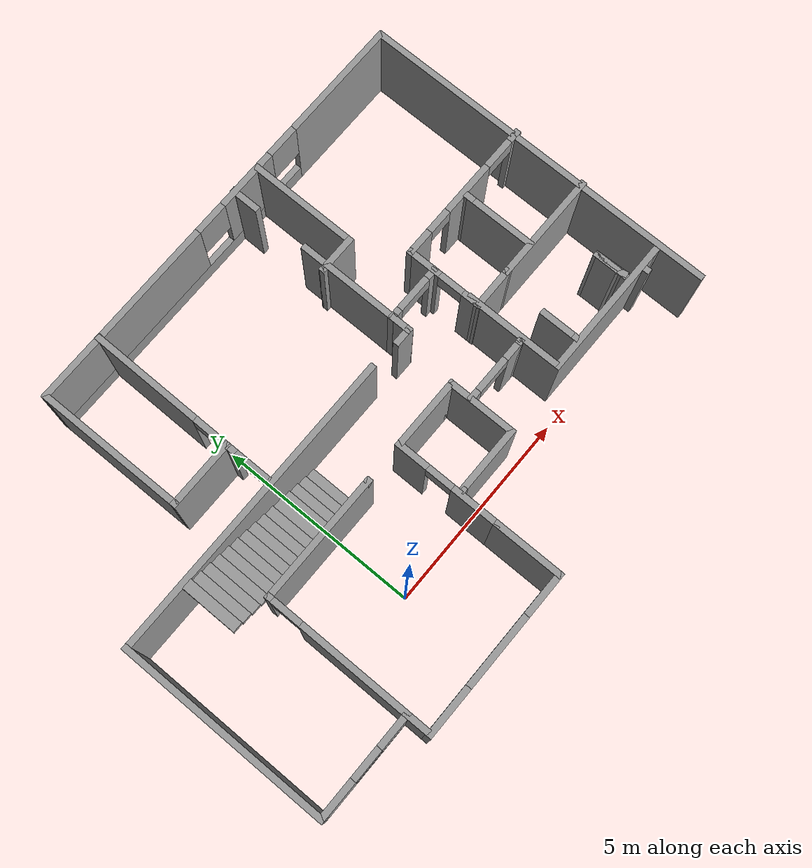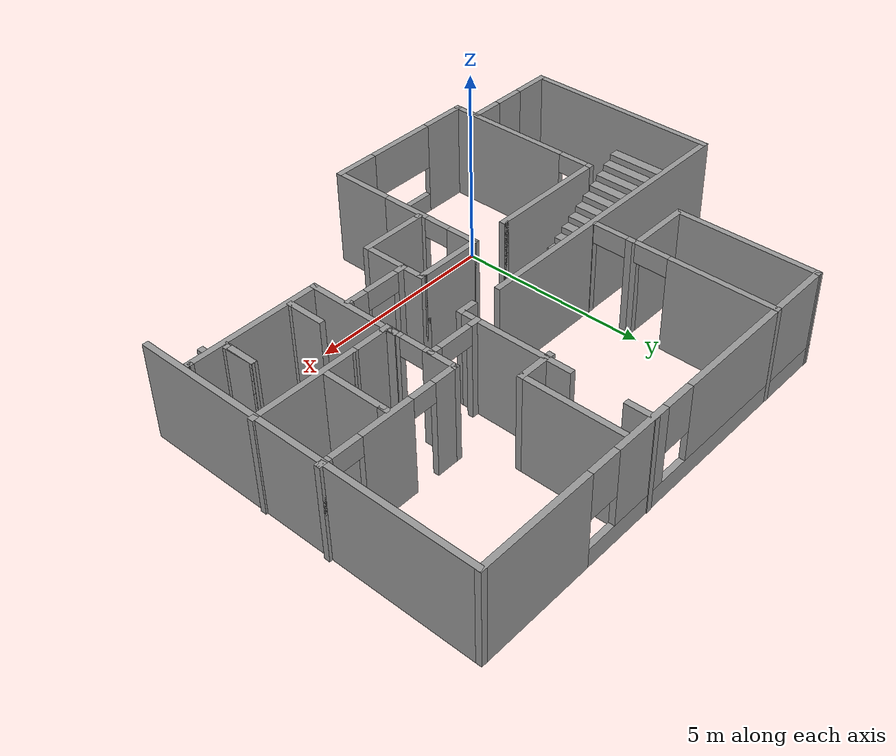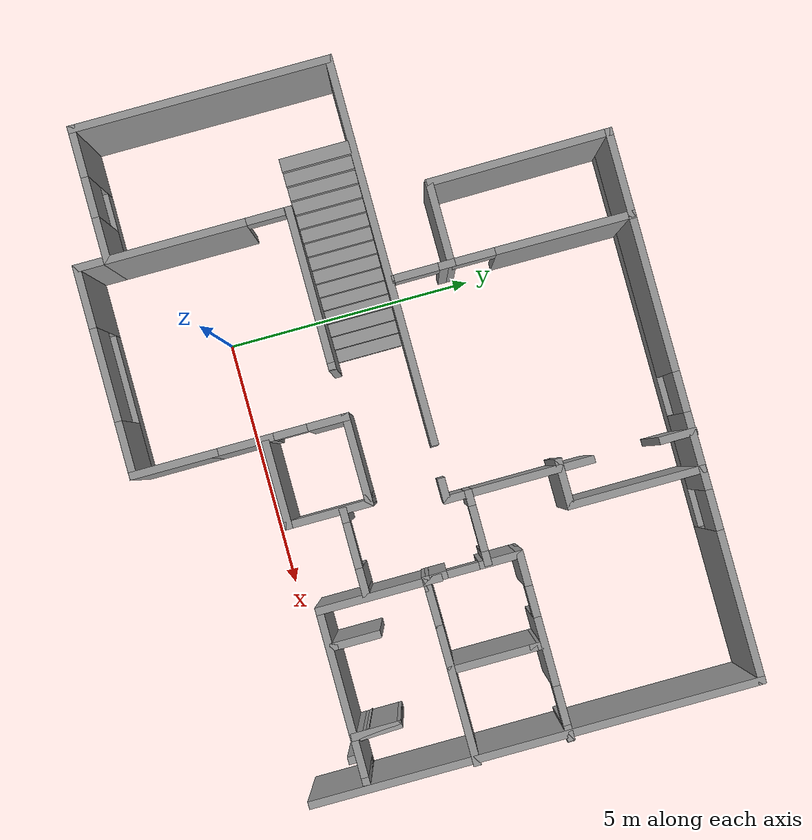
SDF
<?xml version='1.0'?>
<sdf version='1.7'>
  <model name='Floorplan4'>
    <pose>2.26268 3.01833 0 0 -0 0</pose>

    <link name='Stairs_0'>
      <visual name='Stairs_0_Visual_0'>
        <pose>-1.48224 -0.300305 0.083333 0 -0 -1.5708</pose>
        <geometry>
          <box>
            <size>1.373 0.259133 0.166667</size>
          </box>
        </geometry>
        <material>
          <script>
            <uri>file://media/materials/scripts/gazebo.material</uri>
            <name>Gazebo/Grey</name>
          </script>
          <ambient>1 1 1 1</ambient>
        </material>
        <meta>
          <layer>0</layer>
        </meta>
      </visual>
      <collision name='Stairs_0_Collision_0'>
        <geometry>
          <box>
            <size>1.373 0.259133 0.166667</size>
          </box>
        </geometry>
        <pose>-1.48224 -0.300305 0.083333 0 -0 -1.5708</pose>
      </collision>
      <visual name='Stairs_0_Visual_1'>
        <pose>-1.74138 -0.300305 0.25 0 -0 -1.5708</pose>
        <geometry>
          <box>
            <size>1.373 0.259133 0.166667</size>
          </box>
        </geometry>
        <material>
          <script>
            <uri>file://media/materials/scripts/gazebo.material</uri>
            <name>Gazebo/Grey</name>
          </script>
          <ambient>1 1 1 1</ambient>
        </material>
        <meta>
          <layer>0</layer>
        </meta>
      </visual>
      <collision name='Stairs_0_Collision_1'>
        <geometry>
          <box>
            <size>1.373 0.259133 0.166667</size>
          </box>
        </geometry>
        <pose>-1.74138 -0.300305 0.25 0 -0 -1.5708</pose>
      </collision>
      <visual name='Stairs_0_Visual_2'>
        <pose>-2.00051 -0.300305 0.416667 0 -0 -1.5708</pose>
        <geometry>
          <box>
            <size>1.373 0.259133 0.166667</size>
          </box>
        </geometry>
        <material>
          <script>
            <uri>file://media/materials/scripts/gazebo.material</uri>
            <name>Gazebo/Grey</name>
          </script>
          <ambient>1 1 1 1</ambient>
        </material>
        <meta>
          <layer>0</layer>
        </meta>
      </visual>
      <collision name='Stairs_0_Collision_2'>
        <geometry>
          <box>
            <size>1.373 0.259133 0.166667</size>
          </box>
        </geometry>
        <pose>-2.00051 -0.300305 0.416667 0 -0 -1.5708</pose>
      </collision>
      <visual name='Stairs_0_Visual_3'>
        <pose>-2.25964 -0.300305 0.583333 0 -0 -1.5708</pose>
        <geometry>
          <box>
            <size>1.373 0.259133 0.166667</size>
          </box>
        </geometry>
        <material>
          <script>
            <uri>file://media/materials/scripts/gazebo.material</uri>
            <name>Gazebo/Grey</name>
          </script>
          <ambient>1 1 1 1</ambient>
        </material>
        <meta>
          <layer>0</layer>
        </meta>
      </visual>
      <collision name='Stairs_0_Collision_3'>
        <geometry>
          <box>
            <size>1.373 0.259133 0.166667</size>
          </box>
        </geometry>
        <pose>-2.25964 -0.300305 0.583333 0 -0 -1.5708</pose>
      </collision>
      <visual name='Stairs_0_Visual_4'>
        <pose>-2.51878 -0.300305 0.75 0 -0 -1.5708</pose>
        <geometry>
          <box>
            <size>1.373 0.259133 0.166667</size>
          </box>
        </geometry>
        <material>
          <script>
            <uri>file://media/materials/scripts/gazebo.material</uri>
            <name>Gazebo/Grey</name>
          </script>
          <ambient>1 1 1 1</ambient>
        </material>
        <meta>
          <layer>0</layer>
        </meta>
      </visual>
      <collision name='Stairs_0_Collision_4'>
        <geometry>
          <box>
            <size>1.373 0.259133 0.166667</size>
          </box>
        </geometry>
        <pose>-2.51878 -0.300305 0.75 0 -0 -1.5708</pose>
      </collision>
      <visual name='Stairs_0_Visual_5'>
        <pose>-2.77791 -0.300305 0.916667 0 -0 -1.5708</pose>
        <geometry>
          <box>
            <size>1.373 0.259133 0.166667</size>
          </box>
        </geometry>
        <material>
          <script>
            <uri>file://media/materials/scripts/gazebo.material</uri>
            <name>Gazebo/Grey</name>
          </script>
          <ambient>1 1 1 1</ambient>
        </material>
        <meta>
          <layer>0</layer>
        </meta>
      </visual>
      <collision name='Stairs_0_Collision_5'>
        <geometry>
          <box>
            <size>1.373 0.259133 0.166667</size>
          </box>
        </geometry>
        <pose>-2.77791 -0.300305 0.916667 0 -0 -1.5708</pose>
      </collision>
      <visual name='Stairs_0_Visual_6'>
        <pose>-3.03704 -0.300305 1.08333 0 -0 -1.5708</pose>
        <geometry>
          <box>
            <size>1.373 0.259133 0.166667</size>
          </box>
        </geometry>
        <material>
          <script>
            <uri>file://media/materials/scripts/gazebo.material</uri>
            <name>Gazebo/Grey</name>
          </script>
          <ambient>1 1 1 1</ambient>
        </material>
        <meta>
          <layer>0</layer>
        </meta>
      </visual>
      <collision name='Stairs_0_Collision_6'>
        <geometry>
          <box>
            <size>1.373 0.259133 0.166667</size>
          </box>
        </geometry>
        <pose>-3.03704 -0.300305 1.08333 0 -0 -1.5708</pose>
      </collision>
      <visual name='Stairs_0_Visual_7'>
        <pose>-3.29618 -0.300305 1.25 0 -0 -1.5708</pose>
        <geometry>
          <box>
            <size>1.373 0.259133 0.166667</size>
          </box>
        </geometry>
        <material>
          <script>
            <uri>file://media/materials/scripts/gazebo.material</uri>
            <name>Gazebo/Grey</name>
          </script>
          <ambient>1 1 1 1</ambient>
        </material>
        <meta>
          <layer>0</layer>
        </meta>
      </visual>
      <collision name='Stairs_0_Collision_7'>
        <geometry>
          <box>
            <size>1.373 0.259133 0.166667</size>
          </box>
        </geometry>
        <pose>-3.29618 -0.300305 1.25 0 -0 -1.5708</pose>
      </collision>
      <visual name='Stairs_0_Visual_8'>
        <pose>-3.55531 -0.300305 1.41667 0 -0 -1.5708</pose>
        <geometry>
          <box>
            <size>1.373 0.259133 0.166667</size>
          </box>
        </geometry>
        <material>
          <script>
            <uri>file://media/materials/scripts/gazebo.material</uri>
            <name>Gazebo/Grey</name>
          </script>
          <ambient>1 1 1 1</ambient>
        </material>
        <meta>
          <layer>0</layer>
        </meta>
      </visual>
      <collision name='Stairs_0_Collision_8'>
        <geometry>
          <box>
            <size>1.373 0.259133 0.166667</size>
          </box>
        </geometry>
        <pose>-3.55531 -0.300305 1.41667 0 -0 -1.5708</pose>
      </collision>
      <visual name='Stairs_0_Visual_9'>
        <pose>-3.81444 -0.300305 1.58333 0 -0 -1.5708</pose>
        <geometry>
          <box>
            <size>1.373 0.259133 0.166667</size>
          </box>
        </geometry>
        <material>
          <script>
            <uri>file://media/materials/scripts/gazebo.material</uri>
            <name>Gazebo/Grey</name>
          </script>
          <ambient>1 1 1 1</ambient>
        </material>
        <meta>
          <layer>0</layer>
        </meta>
      </visual>
      <collision name='Stairs_0_Collision_9'>
        <geometry>
          <box>
            <size>1.373 0.259133 0.166667</size>
          </box>
        </geometry>
        <pose>-3.81444 -0.300305 1.58333 0 -0 -1.5708</pose>
      </collision>
      <visual name='Stairs_0_Visual_10'>
        <pose>-4.07358 -0.300305 1.75 0 -0 -1.5708</pose>
        <geometry>
          <box>
            <size>1.373 0.259133 0.166667</size>
          </box>
        </geometry>
        <material>
          <script>
            <uri>file://media/materials/scripts/gazebo.material</uri>
            <name>Gazebo/Grey</name>
          </script>
          <ambient>1 1 1 1</ambient>
        </material>
        <meta>
          <layer>0</layer>
        </meta>
      </visual>
      <collision name='Stairs_0_Collision_10'>
        <geometry>
          <box>
            <size>1.373 0.259133 0.166667</size>
          </box>
        </geometry>
        <pose>-4.07358 -0.300305 1.75 0 -0 -1.5708</pose>
      </collision>
      <visual name='Stairs_0_Visual_11'>
        <pose>-4.33271 -0.300305 1.91667 0 -0 -1.5708</pose>
        <geometry>
          <box>
            <size>1.373 0.259133 0.166667</size>
          </box>
        </geometry>
        <material>
          <script>
            <uri>file://media/materials/scripts/gazebo.material</uri>
            <name>Gazebo/Grey</name>
          </script>
          <ambient>1 1 1 1</ambient>
        </material>
        <meta>
          <layer>0</layer>
        </meta>
      </visual>
      <collision name='Stairs_0_Collision_11'>
        <geometry>
          <box>
            <size>1.373 0.259133 0.166667</size>
          </box>
        </geometry>
        <pose>-4.33271 -0.300305 1.91667 0 -0 -1.5708</pose>
      </collision>
      <visual name='Stairs_0_Visual_12'>
        <pose>-4.59184 -0.300305 2.08333 0 -0 -1.5708</pose>
        <geometry>
          <box>
            <size>1.373 0.259133 0.166667</size>
          </box>
        </geometry>
        <material>
          <script>
            <uri>file://media/materials/scripts/gazebo.material</uri>
            <name>Gazebo/Grey</name>
          </script>
          <ambient>1 1 1 1</ambient>
        </material>
        <meta>
          <layer>0</layer>
        </meta>
      </visual>
      <collision name='Stairs_0_Collision_12'>
        <geometry>
          <box>
            <size>1.373 0.259133 0.166667</size>
          </box>
        </geometry>
        <pose>-4.59184 -0.300305 2.08333 0 -0 -1.5708</pose>
      </collision>
      <visual name='Stairs_0_Visual_13'>
        <pose>-4.85098 -0.300305 2.25 0 -0 -1.5708</pose>
        <geometry>
          <box>
            <size>1.373 0.259133 0.166667</size>
          </box>
        </geometry>
        <material>
          <script>
            <uri>file://media/materials/scripts/gazebo.material</uri>
            <name>Gazebo/Grey</name>
          </script>
          <ambient>1 1 1 1</ambient>
        </material>
        <meta>
          <layer>0</layer>
        </meta>
      </visual>
      <collision name='Stairs_0_Collision_13'>
        <geometry>
          <box>
            <size>1.373 0.259133 0.166667</size>
          </box>
        </geometry>
        <pose>-4.85098 -0.300305 2.25 0 -0 -1.5708</pose>
      </collision>
      <visual name='Stairs_0_Visual_14'>
        <pose>-5.11011 -0.300305 2.41667 0 -0 -1.5708</pose>
        <geometry>
          <box>
            <size>1.373 0.259133 0.166667</size>
          </box>
        </geometry>
        <material>
          <script>
            <uri>file://media/materials/scripts/gazebo.material</uri>
            <name>Gazebo/Grey</name>
          </script>
          <ambient>1 1 1 1</ambient>
        </material>
        <meta>
          <layer>0</layer>
        </meta>
      </visual>
      <collision name='Stairs_0_Collision_14'>
        <geometry>
          <box>
            <size>1.373 0.259133 0.166667</size>
          </box>
        </geometry>
        <pose>-5.11011 -0.300305 2.41667 0 -0 -1.5708</pose>
      </collision>
    </link>
    <link name='Wall_0'>
      <collision name='Wall_0_Collision'>
        <geometry>
          <box>
            <size>9 0.15 2.5</size>
          </box>
        </geometry>
        <pose>0 0 1.25 0 -0 0</pose>
      </collision>
      <visual name='Wall_0_Visual'>
        <pose>0 0 1.25 0 -0 0</pose>
        <geometry>
          <box>
            <size>9 0.15 2.5</size>
          </box>
        </geometry>
        <material>
          <script>
            <uri>file://media/materials/scripts/gazebo.material</uri>
            <name>Gazebo/Grey</name>
          </script>
          <ambient>1 1 1 1</ambient>
        </material>
        <meta>
          <layer>0</layer>
        </meta>
      </visual>
      <pose>6.77354 0.814241 0 0 -0 1.5708</pose>
    </link>
    <link name='Wall_11'>
      <collision name='Wall_11_Collision'>
        <geometry>
          <box>
            <size>0.75 0.15 2.5</size>
          </box>
        </geometry>
        <pose>0 0 1.25 0 -0 0</pose>
      </collision>
      <visual name='Wall_11_Visual'>
        <pose>0 0 1.25 0 -0 0</pose>
        <geometry>
          <box>
            <size>0.75 0.15 2.5</size>
          </box>
        </geometry>
        <material>
          <script>
            <uri>file://media/materials/scripts/gazebo.material</uri>
            <name>Gazebo/Grey</name>
          </script>
          <ambient>1 1 1 1</ambient>
        </material>
        <meta>
          <layer>0</layer>
        </meta>
      </visual>
      <pose>1.87688 4.95601 0 0 -0 1.5708</pose>
    </link>
    <link name='Wall_13'>
      <collision name='Wall_13_Collision'>
        <geometry>
          <box>
            <size>2.75 0.15 2.5</size>
          </box>
        </geometry>
        <pose>0 0 1.25 0 -0 0</pose>
      </collision>
      <visual name='Wall_13_Visual'>
        <pose>0 0 1.25 0 -0 0</pose>
        <geometry>
          <box>
            <size>2.75 0.15 2.5</size>
          </box>
        </geometry>
        <material>
          <script>
            <uri>file://media/materials/scripts/gazebo.material</uri>
            <name>Gazebo/Grey</name>
          </script>
          <ambient>1 1 1 1</ambient>
        </material>
        <meta>
          <layer>0</layer>
        </meta>
      </visual>
      <pose>2.60855 3.92948 0 0 -0 -1.5708</pose>
    </link>
    <link name='Wall_14'>
      <collision name='Wall_14_Collision'>
        <geometry>
          <box>
            <size>1 0.15 2.5</size>
          </box>
        </geometry>
        <pose>0 0 1.25 0 -0 0</pose>
      </collision>
      <visual name='Wall_14_Visual'>
        <pose>0 0 1.25 0 -0 0</pose>
        <geometry>
          <box>
            <size>1 0.15 2.5</size>
          </box>
        </geometry>
        <material>
          <script>
            <uri>file://media/materials/scripts/gazebo.material</uri>
            <name>Gazebo/Grey</name>
          </script>
          <ambient>1 1 1 1</ambient>
        </material>
        <meta>
          <layer>0</layer>
        </meta>
      </visual>
      <pose>2.18355 2.62948 0 0 -0 3.14159</pose>
    </link>
    <link name='Wall_15'>
      <collision name='Wall_15_Collision'>
        <geometry>
          <box>
            <size>0.15 0.15 2.5</size>
          </box>
        </geometry>
        <pose>0 0 1.25 0 -0 0</pose>
      </collision>
      <visual name='Wall_15_Visual'>
        <pose>0 0 1.25 0 -0 0</pose>
        <geometry>
          <box>
            <size>0.15 0.15 2.5</size>
          </box>
        </geometry>
        <material>
          <script>
            <uri>file://media/materials/scripts/gazebo.material</uri>
            <name>Gazebo/Grey</name>
          </script>
          <ambient>1 1 1 1</ambient>
        </material>
        <meta>
          <layer>0</layer>
        </meta>
      </visual>
      <pose>1.75855 2.62948 0 0 -0 0</pose>
    </link>
    <link name='Wall_17'>
      <collision name='Wall_17_Collision'>
        <geometry>
          <box>
            <size>3 0.15 2.5</size>
          </box>
        </geometry>
        <pose>0 0 1.25 0 -0 0</pose>
      </collision>
      <visual name='Wall_17_Visual'>
        <pose>0 0 1.25 0 -0 0</pose>
        <geometry>
          <box>
            <size>3 0.15 2.5</size>
          </box>
        </geometry>
        <material>
          <script>
            <uri>file://media/materials/scripts/gazebo.material</uri>
            <name>Gazebo/Grey</name>
          </script>
          <ambient>1 1 1 1</ambient>
        </material>
        <meta>
          <layer>0</layer>
        </meta>
      </visual>
      <pose>1.87688 1.80723 0 0 -0 -1.5708</pose>
    </link>
    <link name='Wall_18'>
      <collision name='Wall_18_Collision'>
        <geometry>
          <box>
            <size>0.5 0.15 2.5</size>
          </box>
        </geometry>
        <pose>0 0 1.25 0 -0 0</pose>
      </collision>
      <visual name='Wall_18_Visual'>
        <pose>0 0 1.25 0 -0 0</pose>
        <geometry>
          <box>
            <size>0.5 0.15 2.5</size>
          </box>
        </geometry>
        <material>
          <script>
            <uri>file://media/materials/scripts/gazebo.material</uri>
            <name>Gazebo/Grey</name>
          </script>
          <ambient>1 1 1 1</ambient>
        </material>
        <meta>
          <layer>0</layer>
        </meta>
      </visual>
      <pose>1.70188 0.38223 0 0 -0 3.14159</pose>
    </link>
    <link name='Wall_20'>
      <collision name='Wall_20_Collision'>
        <geometry>
          <box>
            <size>7.75 0.15 2.5</size>
          </box>
        </geometry>
        <pose>0 0 1.25 0 -0 0</pose>
      </collision>
      <visual name='Wall_20_Visual'>
        <pose>0 0 1.25 0 -0 0</pose>
        <geometry>
          <box>
            <size>7.75 0.15 2.5</size>
          </box>
        </geometry>
        <material>
          <script>
            <uri>file://media/materials/scripts/gazebo.material</uri>
            <name>Gazebo/Grey</name>
          </script>
          <ambient>1 1 1 1</ambient>
        </material>
        <meta>
          <layer>0</layer>
        </meta>
      </visual>
      <pose>-3.05028 0.443986 0 0 -0 3.14159</pose>
    </link>
    <link name='Wall_21'>
      <collision name='Wall_21_Collision'>
        <geometry>
          <box>
            <size>5.25 0.15 2.5</size>
          </box>
        </geometry>
        <pose>0 0 1.25 0 -0 0</pose>
      </collision>
      <visual name='Wall_21_Visual'>
        <pose>0 0 1.25 0 -0 0</pose>
        <geometry>
          <box>
            <size>5.25 0.15 2.5</size>
          </box>
        </geometry>
        <material>
          <script>
            <uri>file://media/materials/scripts/gazebo.material</uri>
            <name>Gazebo/Grey</name>
          </script>
          <ambient>1 1 1 1</ambient>
        </material>
        <meta>
          <layer>0</layer>
        </meta>
      </visual>
      <pose>-6.85028 -2.10601 0 0 -0 -1.5708</pose>
    </link>
    <link name='Wall_22'>
      <pose>-5.55028 -4.65601 0 0 -0 0</pose>
      <visual name='Wall_22_Visual_0'>
        <pose>-0.858994 0 1.25 0 -0 0</pose>
        <geometry>
          <box>
            <size>1.03201 0.15 2.5</size>
          </box>
        </geometry>
        <material>
          <script>
            <uri>file://media/materials/scripts/gazebo.material</uri>
            <name>Gazebo/Grey</name>
          </script>
          <ambient>1 1 1 1</ambient>
        </material>
        <meta>
          <layer>0</layer>
        </meta>
      </visual>
      <collision name='Wall_22_Collision_0'>
        <geometry>
          <box>
            <size>1.03201 0.15 2.5</size>
          </box>
        </geometry>
        <pose>-0.858994 0 1.25 0 -0 0</pose>
      </collision>
      <visual name='Wall_22_Visual_1'>
        <pose>0.516006 0 0.25 0 -0 0</pose>
        <geometry>
          <box>
            <size>1.71799 0.15 0.5</size>
          </box>
        </geometry>
        <material>
          <script>
            <uri>file://media/materials/scripts/gazebo.material</uri>
            <name>Gazebo/Grey</name>
          </script>
          <ambient>1 1 1 1</ambient>
        </material>
        <meta>
          <layer>0</layer>
        </meta>
      </visual>
      <collision name='Wall_22_Collision_1'>
        <geometry>
          <box>
            <size>1.71799 0.15 0.5</size>
          </box>
        </geometry>
        <pose>0.516006 0 0.25 0 -0 0</pose>
      </collision>
      <visual name='Wall_22_Visual_2'>
        <pose>0.916006 0 1.5 0 -0 0</pose>
        <geometry>
          <box>
            <size>0.917989 0.15 2</size>
          </box>
        </geometry>
        <material>
          <script>
            <uri>file://media/materials/scripts/gazebo.material</uri>
            <name>Gazebo/Grey</name>
          </script>
          <ambient>1 1 1 1</ambient>
        </material>
        <meta>
          <layer>0</layer>
        </meta>
      </visual>
      <collision name='Wall_22_Collision_2'>
        <geometry>
          <box>
            <size>0.917989 0.15 2</size>
          </box>
        </geometry>
        <pose>0.916006 0 1.5 0 -0 0</pose>
      </collision>
      <visual name='Wall_22_Visual_3'>
        <pose>0.057011 0 1.9 0 -0 0</pose>
        <geometry>
          <box>
            <size>0.8 0.15 1.2</size>
          </box>
        </geometry>
        <material>
          <script>
            <uri>file://media/materials/scripts/gazebo.material</uri>
            <name>Gazebo/Grey</name>
          </script>
          <ambient>1 1 1 1</ambient>
        </material>
        <meta>
          <layer>0</layer>
        </meta>
      </visual>
      <collision name='Wall_22_Collision_3'>
        <geometry>
          <box>
            <size>0.8 0.15 1.2</size>
          </box>
        </geometry>
        <pose>0.057011 0 1.9 0 -0 0</pose>
      </collision>
    </link>
    <link name='Wall_23'>
      <collision name='Wall_23_Collision'>
        <geometry>
          <box>
            <size>0.75 0.15 2.5</size>
          </box>
        </geometry>
        <pose>0 0 1.25 0 -0 0</pose>
      </collision>
      <visual name='Wall_23_Visual'>
        <pose>0 0 1.25 0 -0 0</pose>
        <geometry>
          <box>
            <size>0.75 0.15 2.5</size>
          </box>
        </geometry>
        <material>
          <script>
            <uri>file://media/materials/scripts/gazebo.material</uri>
            <name>Gazebo/Grey</name>
          </script>
          <ambient>1 1 1 1</ambient>
        </material>
        <meta>
          <layer>0</layer>
        </meta>
      </visual>
      <pose>-4.25028 -4.95601 0 0 -0 -1.5708</pose>
    </link>
    <link name='Wall_24'>
      <pose>-2.20028 -5.25601 0 0 -0 0</pose>
      <visual name='Wall_24_Visual_0'>
        <pose>-1.49218 0 1.25 0 -0 0</pose>
        <geometry>
          <box>
            <size>1.26565 0.15 2.5</size>
          </box>
        </geometry>
        <material>
          <script>
            <uri>file://media/materials/scripts/gazebo.material</uri>
            <name>Gazebo/Grey</name>
          </script>
          <ambient>1 1 1 1</ambient>
        </material>
        <meta>
          <layer>0</layer>
        </meta>
      </visual>
      <collision name='Wall_24_Collision_0'>
        <geometry>
          <box>
            <size>1.26565 0.15 2.5</size>
          </box>
        </geometry>
        <pose>-1.49218 0 1.25 0 -0 0</pose>
      </collision>
      <visual name='Wall_24_Visual_1'>
        <pose>0.632824 0 0.25 0 -0 0</pose>
        <geometry>
          <box>
            <size>2.98435 0.15 0.5</size>
          </box>
        </geometry>
        <material>
          <script>
            <uri>file://media/materials/scripts/gazebo.material</uri>
            <name>Gazebo/Grey</name>
          </script>
          <ambient>1 1 1 1</ambient>
        </material>
        <meta>
          <layer>0</layer>
        </meta>
      </visual>
      <collision name='Wall_24_Collision_1'>
        <geometry>
          <box>
            <size>2.98435 0.15 0.5</size>
          </box>
        </geometry>
        <pose>0.632824 0 0.25 0 -0 0</pose>
      </collision>
      <visual name='Wall_24_Visual_2'>
        <pose>1.55421 0 1.5 0 -0 0</pose>
        <geometry>
          <box>
            <size>1.14157 0.15 2</size>
          </box>
        </geometry>
        <material>
          <script>
            <uri>file://media/materials/scripts/gazebo.material</uri>
            <name>Gazebo/Grey</name>
          </script>
          <ambient>1 1 1 1</ambient>
        </material>
        <meta>
          <layer>0</layer>
        </meta>
      </visual>
      <collision name='Wall_24_Collision_2'>
        <geometry>
          <box>
            <size>1.14157 0.15 2</size>
          </box>
        </geometry>
        <pose>1.55421 0 1.5 0 -0 0</pose>
      </collision>
      <visual name='Wall_24_Visual_3'>
        <pose>0.062037 0 1.9 0 -0 0</pose>
        <geometry>
          <box>
            <size>1.84278 0.15 1.2</size>
          </box>
        </geometry>
        <material>
          <script>
            <uri>file://media/materials/scripts/gazebo.material</uri>
            <name>Gazebo/Grey</name>
          </script>
          <ambient>1 1 1 1</ambient>
        </material>
        <meta>
          <layer>0</layer>
        </meta>
      </visual>
      <collision name='Wall_24_Collision_3'>
        <geometry>
          <box>
            <size>1.84278 0.15 1.2</size>
          </box>
        </geometry>
        <pose>0.062037 0 1.9 0 -0 0</pose>
      </collision>
    </link>
    <link name='Wall_25'>
      <collision name='Wall_25_Collision'>
        <geometry>
          <box>
            <size>1.75 0.15 2.5</size>
          </box>
        </geometry>
        <pose>0 0 1.25 0 -0 0</pose>
      </collision>
      <visual name='Wall_25_Visual'>
        <pose>0 0 1.25 0 -0 0</pose>
        <geometry>
          <box>
            <size>1.75 0.15 2.5</size>
          </box>
        </geometry>
        <material>
          <script>
            <uri>file://media/materials/scripts/gazebo.material</uri>
            <name>Gazebo/Grey</name>
          </script>
          <ambient>1 1 1 1</ambient>
        </material>
        <meta>
          <layer>0</layer>
        </meta>
      </visual>
      <pose>-0.150279 -4.45601 0 0 -0 1.5708</pose>
    </link>
    <link name='Wall_26'>
      <pose>-0.150279 -2.35601 0 0 -0 1.5708</pose>
      <visual name='Wall_26_Visual_0'>
        <pose>-0.749014 0 1.25 0 -0 0</pose>
        <geometry>
          <box>
            <size>1.25197 0.15 2.5</size>
          </box>
        </geometry>
        <material>
          <script>
            <uri>file://media/materials/scripts/gazebo.material</uri>
            <name>Gazebo/Grey</name>
          </script>
          <ambient>1 1 1 1</ambient>
        </material>
        <meta>
          <layer>0</layer>
        </meta>
      </visual>
      <collision name='Wall_26_Collision_0'>
        <geometry>
          <box>
            <size>1.25197 0.15 2.5</size>
          </box>
        </geometry>
        <pose>-0.749014 0 1.25 0 -0 0</pose>
      </collision>
      <visual name='Wall_26_Visual_1'>
        <pose>0.956973 0 1.25 0 -0 0</pose>
        <geometry>
          <box>
            <size>0.836053 0.15 2.5</size>
          </box>
        </geometry>
        <material>
          <script>
            <uri>file://media/materials/scripts/gazebo.material</uri>
            <name>Gazebo/Grey</name>
          </script>
          <ambient>1 1 1 1</ambient>
        </material>
        <meta>
          <layer>0</layer>
        </meta>
      </visual>
      <collision name='Wall_26_Collision_1'>
        <geometry>
          <box>
            <size>0.836053 0.15 2.5</size>
          </box>
        </geometry>
        <pose>0.956973 0 1.25 0 -0 0</pose>
      </collision>
      <visual name='Wall_26_Visual_2'>
        <pose>0.20796 0 2.25 0 -0 0</pose>
        <geometry>
          <box>
            <size>0.661975 0.15 0.5</size>
          </box>
        </geometry>
        <material>
          <script>
            <uri>file://media/materials/scripts/gazebo.material</uri>
            <name>Gazebo/Grey</name>
          </script>
          <ambient>1 1 1 1</ambient>
        </material>
        <meta>
          <layer>0</layer>
        </meta>
      </visual>
      <collision name='Wall_26_Collision_2'>
        <geometry>
          <box>
            <size>0.661975 0.15 0.5</size>
          </box>
        </geometry>
        <pose>0.20796 0 2.25 0 -0 0</pose>
      </collision>
    </link>
    <link name='Wall_27'>
      <collision name='Wall_27_Collision'>
        <geometry>
          <box>
            <size>1.75 0.15 2.5</size>
          </box>
        </geometry>
        <pose>0 0 1.25 0 -0 0</pose>
      </collision>
      <visual name='Wall_27_Visual'>
        <pose>0 0 1.25 0 -0 0</pose>
        <geometry>
          <box>
            <size>1.75 0.15 2.5</size>
          </box>
        </geometry>
        <material>
          <script>
            <uri>file://media/materials/scripts/gazebo.material</uri>
            <name>Gazebo/Grey</name>
          </script>
          <ambient>1 1 1 1</ambient>
        </material>
        <meta>
          <layer>0</layer>
        </meta>
      </visual>
      <pose>0.649721 -1.05601 0 0 -0 0</pose>
    </link>
    <link name='Wall_28'>
      <collision name='Wall_28_Collision'>
        <geometry>
          <box>
            <size>0.25 0.15 2.5</size>
          </box>
        </geometry>
        <pose>0 0 1.25 0 -0 0</pose>
      </collision>
      <visual name='Wall_28_Visual'>
        <pose>0 0 1.25 0 -0 0</pose>
        <geometry>
          <box>
            <size>0.25 0.15 2.5</size>
          </box>
        </geometry>
        <material>
          <script>
            <uri>file://media/materials/scripts/gazebo.material</uri>
            <name>Gazebo/Grey</name>
          </script>
          <ambient>1 1 1 1</ambient>
        </material>
        <meta>
          <layer>0</layer>
        </meta>
      </visual>
      <pose>1.49972 -1.05601 0 0 -0 0</pose>
    </link>
    <link name='Wall_29'>
      <collision name='Wall_29_Collision'>
        <geometry>
          <box>
            <size>1.75 0.15 2.5</size>
          </box>
        </geometry>
        <pose>0 0 1.25 0 -0 0</pose>
      </collision>
      <visual name='Wall_29_Visual'>
        <pose>0 0 1.25 0 -0 0</pose>
        <geometry>
          <box>
            <size>1.75 0.15 2.5</size>
          </box>
        </geometry>
        <material>
          <script>
            <uri>file://media/materials/scripts/gazebo.material</uri>
            <name>Gazebo/Grey</name>
          </script>
          <ambient>1 1 1 1</ambient>
        </material>
        <meta>
          <layer>0</layer>
        </meta>
      </visual>
      <pose>1.54972 -1.85601 0 0 -0 -1.5708</pose>
    </link>
    <link name='Wall_3'>
      <collision name='Wall_3_Collision'>
        <geometry>
          <box>
            <size>0.15 0.15 2.5</size>
          </box>
        </geometry>
        <pose>0 0 1.25 0 -0 0</pose>
      </collision>
      <visual name='Wall_3_Visual'>
        <pose>0 0 1.25 0 -0 0</pose>
        <geometry>
          <box>
            <size>0.15 0.15 2.5</size>
          </box>
        </geometry>
        <material>
          <script>
            <uri>file://media/materials/scripts/gazebo.material</uri>
            <name>Gazebo/Grey</name>
          </script>
          <ambient>1 1 1 1</ambient>
        </material>
        <meta>
          <layer>0</layer>
        </meta>
      </visual>
      <pose>6.15788 -2.66213 0 0 -0 0</pose>
    </link>
    <link name='Wall_30'>
      <collision name='Wall_30_Collision'>
        <geometry>
          <box>
            <size>1.75 0.15 2.5</size>
          </box>
        </geometry>
        <pose>0 0 1.25 0 -0 0</pose>
      </collision>
      <visual name='Wall_30_Visual'>
        <pose>0 0 1.25 0 -0 0</pose>
        <geometry>
          <box>
            <size>1.75 0.15 2.5</size>
          </box>
        </geometry>
        <material>
          <script>
            <uri>file://media/materials/scripts/gazebo.material</uri>
            <name>Gazebo/Grey</name>
          </script>
          <ambient>1 1 1 1</ambient>
        </material>
        <meta>
          <layer>0</layer>
        </meta>
      </visual>
      <pose>0.749721 -2.65601 0 0 -0 3.14159</pose>
    </link>
    <link name='Wall_31'>
      <collision name='Wall_31_Collision'>
        <geometry>
          <box>
            <size>0.15 0.15 2.5</size>
          </box>
        </geometry>
        <pose>0 0 1.25 0 -0 0</pose>
      </collision>
      <visual name='Wall_31_Visual'>
        <pose>0 0 1.25 0 -0 0</pose>
        <geometry>
          <box>
            <size>0.15 0.15 2.5</size>
          </box>
        </geometry>
        <material>
          <script>
            <uri>file://media/materials/scripts/gazebo.material</uri>
            <name>Gazebo/Grey</name>
          </script>
          <ambient>1 1 1 1</ambient>
        </material>
        <meta>
          <layer>0</layer>
        </meta>
      </visual>
      <pose>-0.050279 -2.65601 0 0 -0 0</pose>
    </link>
    <link name='Wall_33'>
      <pose>-4.25028 -2.85601 0 0 -0 1.5708</pose>
      <visual name='Wall_33_Visual_0'>
        <pose>-0.463048 0 1.25 0 -0 0</pose>
        <geometry>
          <box>
            <size>2.8239 0.15 2.5</size>
          </box>
        </geometry>
        <material>
          <script>
            <uri>file://media/materials/scripts/gazebo.material</uri>
            <name>Gazebo/Grey</name>
          </script>
          <ambient>1 1 1 1</ambient>
        </material>
        <meta>
          <layer>0</layer>
        </meta>
      </visual>
      <collision name='Wall_33_Collision_0'>
        <geometry>
          <box>
            <size>2.8239 0.15 2.5</size>
          </box>
        </geometry>
        <pose>-0.463048 0 1.25 0 -0 0</pose>
      </collision>
      <visual name='Wall_33_Visual_1'>
        <pose>1.7945 0 1.25 0 -0 0</pose>
        <geometry>
          <box>
            <size>0.161005 0.15 2.5</size>
          </box>
        </geometry>
        <material>
          <script>
            <uri>file://media/materials/scripts/gazebo.material</uri>
            <name>Gazebo/Grey</name>
          </script>
          <ambient>1 1 1 1</ambient>
        </material>
        <meta>
          <layer>0</layer>
        </meta>
      </visual>
      <collision name='Wall_33_Collision_1'>
        <geometry>
          <box>
            <size>0.161005 0.15 2.5</size>
          </box>
        </geometry>
        <pose>1.7945 0 1.25 0 -0 0</pose>
      </collision>
      <visual name='Wall_33_Visual_2'>
        <pose>1.33145 0 2.25 0 -0 0</pose>
        <geometry>
          <box>
            <size>0.765091 0.15 0.5</size>
          </box>
        </geometry>
        <material>
          <script>
            <uri>file://media/materials/scripts/gazebo.material</uri>
            <name>Gazebo/Grey</name>
          </script>
          <ambient>1 1 1 1</ambient>
        </material>
        <meta>
          <layer>0</layer>
        </meta>
      </visual>
      <collision name='Wall_33_Collision_2'>
        <geometry>
          <box>
            <size>0.765091 0.15 0.5</size>
          </box>
        </geometry>
        <pose>1.33145 0 2.25 0 -0 0</pose>
      </collision>
    </link>
    <link name='Wall_34'>
      <collision name='Wall_34_Collision'>
        <geometry>
          <box>
            <size>3.25 0.15 2.5</size>
          </box>
        </geometry>
        <pose>0 0 1.25 0 -0 0</pose>
      </collision>
      <visual name='Wall_34_Visual'>
        <pose>0 0 1.25 0 -0 0</pose>
        <geometry>
          <box>
            <size>3.25 0.15 2.5</size>
          </box>
        </geometry>
        <material>
          <script>
            <uri>file://media/materials/scripts/gazebo.material</uri>
            <name>Gazebo/Grey</name>
          </script>
          <ambient>1 1 1 1</ambient>
        </material>
        <meta>
          <layer>0</layer>
        </meta>
      </visual>
      <pose>-2.70028 -1.05601 0 0 -0 0</pose>
    </link>
    <link name='Wall_35'>
      <collision name='Wall_35_Collision'>
        <geometry>
          <box>
            <size>0.15 0.15 2.5</size>
          </box>
        </geometry>
        <pose>0 0 1.25 0 -0 0</pose>
      </collision>
      <visual name='Wall_35_Visual'>
        <pose>0 0 1.25 0 -0 0</pose>
        <geometry>
          <box>
            <size>0.15 0.15 2.5</size>
          </box>
        </geometry>
        <material>
          <script>
            <uri>file://media/materials/scripts/gazebo.material</uri>
            <name>Gazebo/Grey</name>
          </script>
          <ambient>1 1 1 1</ambient>
        </material>
        <meta>
          <layer>0</layer>
        </meta>
      </visual>
      <pose>-1.15028 -1.05601 0 0 -0 0</pose>
    </link>
    <link name='Wall_37'>
      <pose>2.37196 -1.57624 0 0 -0 0</pose>
      <visual name='Wall_37_Visual_0'>
        <pose>-0.726541 0 1.25 0 -0 0</pose>
        <geometry>
          <box>
            <size>0.296918 0.15 2.5</size>
          </box>
        </geometry>
        <material>
          <script>
            <uri>file://media/materials/scripts/gazebo.material</uri>
            <name>Gazebo/Grey</name>
          </script>
          <ambient>1 1 1 1</ambient>
        </material>
        <meta>
          <layer>0</layer>
        </meta>
      </visual>
      <collision name='Wall_37_Collision_0'>
        <geometry>
          <box>
            <size>0.296918 0.15 2.5</size>
          </box>
        </geometry>
        <pose>-0.726541 0 1.25 0 -0 0</pose>
      </collision>
      <visual name='Wall_37_Visual_1'>
        <pose>0.598459 0 1.25 0 -0 0</pose>
        <geometry>
          <box>
            <size>0.553082 0.15 2.5</size>
          </box>
        </geometry>
        <material>
          <script>
            <uri>file://media/materials/scripts/gazebo.material</uri>
            <name>Gazebo/Grey</name>
          </script>
          <ambient>1 1 1 1</ambient>
        </material>
        <meta>
          <layer>0</layer>
        </meta>
      </visual>
      <collision name='Wall_37_Collision_1'>
        <geometry>
          <box>
            <size>0.553082 0.15 2.5</size>
          </box>
        </geometry>
        <pose>0.598459 0 1.25 0 -0 0</pose>
      </collision>
      <visual name='Wall_37_Visual_2'>
        <pose>-0.128082 0 2.25 0 -0 0</pose>
        <geometry>
          <box>
            <size>0.9 0.15 0.5</size>
          </box>
        </geometry>
        <material>
          <script>
            <uri>file://media/materials/scripts/gazebo.material</uri>
            <name>Gazebo/Grey</name>
          </script>
          <ambient>1 1 1 1</ambient>
        </material>
        <meta>
          <layer>0</layer>
        </meta>
      </visual>
      <collision name='Wall_37_Collision_2'>
        <geometry>
          <box>
            <size>0.9 0.15 0.5</size>
          </box>
        </geometry>
        <pose>-0.128082 0 2.25 0 -0 0</pose>
      </collision>
    </link>
    <link name='Wall_38'>
      <collision name='Wall_38_Collision'>
        <geometry>
          <box>
            <size>0.15 0.15 2.5</size>
          </box>
        </geometry>
        <pose>0 0 1.25 0 -0 0</pose>
      </collision>
      <visual name='Wall_38_Visual'>
        <pose>0 0 1.25 0 -0 0</pose>
        <geometry>
          <box>
            <size>0.15 0.15 2.5</size>
          </box>
        </geometry>
        <material>
          <script>
            <uri>file://media/materials/scripts/gazebo.material</uri>
            <name>Gazebo/Grey</name>
          </script>
          <ambient>1 1 1 1</ambient>
        </material>
        <meta>
          <layer>0</layer>
        </meta>
      </visual>
      <pose>3.18182 -1.57624 0 0 -0 0</pose>
    </link>
    <link name='Wall_40'>
      <collision name='Wall_40_Collision'>
        <geometry>
          <box>
            <size>2.5 0.15 2.5</size>
          </box>
        </geometry>
        <pose>0 0 1.25 0 -0 0</pose>
      </collision>
      <visual name='Wall_40_Visual'>
        <pose>0 0 1.25 0 -0 0</pose>
        <geometry>
          <box>
            <size>2.5 0.15 2.5</size>
          </box>
        </geometry>
        <material>
          <script>
            <uri>file://media/materials/scripts/gazebo.material</uri>
            <name>Gazebo/Grey</name>
          </script>
          <ambient>1 1 1 1</ambient>
        </material>
        <meta>
          <layer>0</layer>
        </meta>
      </visual>
      <pose>3.27302 -1.3413 0 0 -0 -1.5708</pose>
    </link>
    <link name='Wall_41'>
      <collision name='Wall_41_Collision'>
        <geometry>
          <box>
            <size>3.5 0.15 2.5</size>
          </box>
        </geometry>
        <pose>0 0 1.25 0 -0 0</pose>
      </collision>
      <visual name='Wall_41_Visual'>
        <pose>0 0 1.25 0 -0 0</pose>
        <geometry>
          <box>
            <size>3.5 0.15 2.5</size>
          </box>
        </geometry>
        <material>
          <script>
            <uri>file://media/materials/scripts/gazebo.material</uri>
            <name>Gazebo/Grey</name>
          </script>
          <ambient>1 1 1 1</ambient>
        </material>
        <meta>
          <layer>0</layer>
        </meta>
      </visual>
      <pose>4.94802 -2.5163 0 0 -0 0</pose>
    </link>
    <link name='Wall_42'>
      <collision name='Wall_42_Collision'>
        <geometry>
          <box>
            <size>0.15 0.15 2.5</size>
          </box>
        </geometry>
        <pose>0 0 1.25 0 -0 0</pose>
      </collision>
      <visual name='Wall_42_Visual'>
        <pose>0 0 1.25 0 -0 0</pose>
        <geometry>
          <box>
            <size>0.15 0.15 2.5</size>
          </box>
        </geometry>
        <material>
          <script>
            <uri>file://media/materials/scripts/gazebo.material</uri>
            <name>Gazebo/Grey</name>
          </script>
          <ambient>1 1 1 1</ambient>
        </material>
        <meta>
          <layer>0</layer>
        </meta>
      </visual>
      <pose>6.62302 -2.5163 0 0 -0 0</pose>
    </link>
    <link name='Wall_44'>
      <collision name='Wall_44_Collision'>
        <geometry>
          <box>
            <size>1 0.15 2.5</size>
          </box>
        </geometry>
        <pose>0 0 1.25 0 -0 0</pose>
      </collision>
      <visual name='Wall_44_Visual'>
        <pose>0 0 1.25 0 -0 0</pose>
        <geometry>
          <box>
            <size>1 0.15 2.5</size>
          </box>
        </geometry>
        <material>
          <script>
            <uri>file://media/materials/scripts/gazebo.material</uri>
            <name>Gazebo/Grey</name>
          </script>
          <ambient>1 1 1 1</ambient>
        </material>
        <meta>
          <layer>0</layer>
        </meta>
      </visual>
      <pose>4.00073 -2.00124 0 0 -0 -1.5708</pose>
    </link>
    <link name='Wall_45'>
      <collision name='Wall_45_Collision'>
        <geometry>
          <box>
            <size>0.15 0.15 2.5</size>
          </box>
        </geometry>
        <pose>0 0 1.25 0 -0 0</pose>
      </collision>
      <visual name='Wall_45_Visual'>
        <pose>0 0 1.25 0 -0 0</pose>
        <geometry>
          <box>
            <size>0.15 0.15 2.5</size>
          </box>
        </geometry>
        <material>
          <script>
            <uri>file://media/materials/scripts/gazebo.material</uri>
            <name>Gazebo/Grey</name>
          </script>
          <ambient>1 1 1 1</ambient>
        </material>
        <meta>
          <layer>0</layer>
        </meta>
      </visual>
      <pose>4.00073 -2.42624 0 0 -0 0</pose>
    </link>
    <link name='Wall_47'>
      <collision name='Wall_47_Collision'>
        <geometry>
          <box>
            <size>0.75 0.15 2.5</size>
          </box>
        </geometry>
        <pose>0 0 1.25 0 -0 0</pose>
      </collision>
      <visual name='Wall_47_Visual'>
        <pose>0 0 1.25 0 -0 0</pose>
        <geometry>
          <box>
            <size>0.75 0.15 2.5</size>
          </box>
        </geometry>
        <material>
          <script>
            <uri>file://media/materials/scripts/gazebo.material</uri>
            <name>Gazebo/Grey</name>
          </script>
          <ambient>1 1 1 1</ambient>
        </material>
        <meta>
          <layer>0</layer>
        </meta>
      </visual>
      <pose>5.75179 -1.94446 0 0 -0 -1.5708</pose>
    </link>
    <link name='Wall_48'>
      <collision name='Wall_48_Collision'>
        <geometry>
          <box>
            <size>0.25 0.15 2.5</size>
          </box>
        </geometry>
        <pose>0 0 1.25 0 -0 0</pose>
      </collision>
      <visual name='Wall_48_Visual'>
        <pose>0 0 1.25 0 -0 0</pose>
        <geometry>
          <box>
            <size>0.25 0.15 2.5</size>
          </box>
        </geometry>
        <material>
          <script>
            <uri>file://media/materials/scripts/gazebo.material</uri>
            <name>Gazebo/Grey</name>
          </script>
          <ambient>1 1 1 1</ambient>
        </material>
        <meta>
          <layer>0</layer>
        </meta>
      </visual>
      <pose>5.76473 -2.29276 0 0 -0 -1.309</pose>
    </link>
    <link name='Wall_5'>
      <pose>1.34854 5.23924 0 0 -0 3.14159</pose>
      <visual name='Wall_5_Visual_0'>
        <pose>-3.98357 0 1.25 0 -0 0</pose>
        <geometry>
          <box>
            <size>3.03285 0.15 2.5</size>
          </box>
        </geometry>
        <material>
          <script>
            <uri>file://media/materials/scripts/gazebo.material</uri>
            <name>Gazebo/Grey</name>
          </script>
          <ambient>1 1 1 1</ambient>
        </material>
        <meta>
          <layer>0</layer>
        </meta>
      </visual>
      <collision name='Wall_5_Collision_0'>
        <geometry>
          <box>
            <size>3.03285 0.15 2.5</size>
          </box>
        </geometry>
        <pose>-3.98357 0 1.25 0 -0 0</pose>
      </collision>
      <visual name='Wall_5_Visual_1'>
        <pose>1.51643 0 0.25 0 -0 0</pose>
        <geometry>
          <box>
            <size>7.96715 0.15 0.5</size>
          </box>
        </geometry>
        <material>
          <script>
            <uri>file://media/materials/scripts/gazebo.material</uri>
            <name>Gazebo/Grey</name>
          </script>
          <ambient>1 1 1 1</ambient>
        </material>
        <meta>
          <layer>0</layer>
        </meta>
      </visual>
      <collision name='Wall_5_Collision_1'>
        <geometry>
          <box>
            <size>7.96715 0.15 0.5</size>
          </box>
        </geometry>
        <pose>1.51643 0 0.25 0 -0 0</pose>
      </collision>
      <visual name='Wall_5_Visual_2'>
        <pose>-0.899688 0 1.5 0 -0 0</pose>
        <geometry>
          <box>
            <size>1.53492 0.15 2</size>
          </box>
        </geometry>
        <material>
          <script>
            <uri>file://media/materials/scripts/gazebo.material</uri>
            <name>Gazebo/Grey</name>
          </script>
          <ambient>1 1 1 1</ambient>
        </material>
        <meta>
          <layer>0</layer>
        </meta>
      </visual>
      <collision name='Wall_5_Collision_2'>
        <geometry>
          <box>
            <size>1.53492 0.15 2</size>
          </box>
        </geometry>
        <pose>-0.899688 0 1.5 0 -0 0</pose>
      </collision>
      <visual name='Wall_5_Visual_3'>
        <pose>3.08388 0 1.5 0 -0 0</pose>
        <geometry>
          <box>
            <size>4.83223 0.15 2</size>
          </box>
        </geometry>
        <material>
          <script>
            <uri>file://media/materials/scripts/gazebo.material</uri>
            <name>Gazebo/Grey</name>
          </script>
          <ambient>1 1 1 1</ambient>
        </material>
        <meta>
          <layer>0</layer>
        </meta>
      </visual>
      <collision name='Wall_5_Collision_3'>
        <geometry>
          <box>
            <size>4.83223 0.15 2</size>
          </box>
        </geometry>
        <pose>3.08388 0 1.5 0 -0 0</pose>
      </collision>
      <visual name='Wall_5_Visual_4'>
        <pose>-2.06715 0 1.9 0 -0 0</pose>
        <geometry>
          <box>
            <size>0.8 0.15 1.2</size>
          </box>
        </geometry>
        <material>
          <script>
            <uri>file://media/materials/scripts/gazebo.material</uri>
            <name>Gazebo/Grey</name>
          </script>
          <ambient>1 1 1 1</ambient>
        </material>
        <meta>
          <layer>0</layer>
        </meta>
      </visual>
      <collision name='Wall_5_Collision_4'>
        <geometry>
          <box>
            <size>0.8 0.15 1.2</size>
          </box>
        </geometry>
        <pose>-2.06715 0 1.9 0 -0 0</pose>
      </collision>
      <visual name='Wall_5_Visual_5'>
        <pose>0.26777 0 1.9 0 -0 0</pose>
        <geometry>
          <box>
            <size>0.8 0.15 1.2</size>
          </box>
        </geometry>
        <material>
          <script>
            <uri>file://media/materials/scripts/gazebo.material</uri>
            <name>Gazebo/Grey</name>
          </script>
          <ambient>1 1 1 1</ambient>
        </material>
        <meta>
          <layer>0</layer>
        </meta>
      </visual>
      <collision name='Wall_5_Collision_5'>
        <geometry>
          <box>
            <size>0.8 0.15 1.2</size>
          </box>
        </geometry>
        <pose>0.26777 0 1.9 0 -0 0</pose>
      </collision>
    </link>
    <link name='Wall_50'>
      <collision name='Wall_50_Collision'>
        <geometry>
          <box>
            <size>0.847073 0.15 2.5</size>
          </box>
        </geometry>
        <pose>0 0 1.25 0 -0 0</pose>
      </collision>
      <visual name='Wall_50_Visual'>
        <pose>0 0 1.25 0 -0 0</pose>
        <geometry>
          <box>
            <size>0.847073 0.15 2.5</size>
          </box>
        </geometry>
        <material>
          <script>
            <uri>file://media/materials/scripts/gazebo.material</uri>
            <name>Gazebo/Grey</name>
          </script>
          <ambient>1 1 1 1</ambient>
        </material>
        <meta>
          <layer>0</layer>
        </meta>
      </visual>
      <pose>5.76473 -1.99276 0 0 -0 1.60793</pose>
    </link>
    <link name='Wall_51'>
      <collision name='Wall_51_Collision'>
        <geometry>
          <box>
            <size>1 0.15 2.5</size>
          </box>
        </geometry>
        <pose>0 0 1.25 0 -0 0</pose>
      </collision>
      <visual name='Wall_51_Visual'>
        <pose>0 0 1.25 0 -0 0</pose>
        <geometry>
          <box>
            <size>1 0.15 2.5</size>
          </box>
        </geometry>
        <material>
          <script>
            <uri>file://media/materials/scripts/gazebo.material</uri>
            <name>Gazebo/Grey</name>
          </script>
          <ambient>1 1 1 1</ambient>
        </material>
        <meta>
          <layer>0</layer>
        </meta>
      </visual>
      <pose>5.75179 -2.06946 0 0 -0 -1.5708</pose>
    </link>
    <link name='Wall_52'>
      <collision name='Wall_52_Collision'>
        <geometry>
          <box>
            <size>0.15 0.15 2.5</size>
          </box>
        </geometry>
        <pose>0 0 1.25 0 -0 0</pose>
      </collision>
      <visual name='Wall_52_Visual'>
        <pose>0 0 1.25 0 -0 0</pose>
        <geometry>
          <box>
            <size>0.15 0.15 2.5</size>
          </box>
        </geometry>
        <material>
          <script>
            <uri>file://media/materials/scripts/gazebo.material</uri>
            <name>Gazebo/Grey</name>
          </script>
          <ambient>1 1 1 1</ambient>
        </material>
        <meta>
          <layer>0</layer>
        </meta>
      </visual>
      <pose>5.75179 -2.49446 0 0 -0 0</pose>
    </link>
    <link name='Wall_54'>
      <collision name='Wall_54_Collision'>
        <geometry>
          <box>
            <size>2.75 0.15 2.5</size>
          </box>
        </geometry>
        <pose>0 0 1.25 0 -0 0</pose>
      </collision>
      <visual name='Wall_54_Visual'>
        <pose>0 0 1.25 0 -0 0</pose>
        <geometry>
          <box>
            <size>2.75 0.15 2.5</size>
          </box>
        </geometry>
        <material>
          <script>
            <uri>file://media/materials/scripts/gazebo.material</uri>
            <name>Gazebo/Grey</name>
          </script>
          <ambient>1 1 1 1</ambient>
        </material>
        <meta>
          <layer>0</layer>
        </meta>
      </visual>
      <pose>5.52062 -0.393709 0 0 -0 3.14159</pose>
    </link>
    <link name='Wall_55'>
      <collision name='Wall_55_Collision'>
        <geometry>
          <box>
            <size>0.15 0.15 2.5</size>
          </box>
        </geometry>
        <pose>0 0 1.25 0 -0 0</pose>
      </collision>
      <visual name='Wall_55_Visual'>
        <pose>0 0 1.25 0 -0 0</pose>
        <geometry>
          <box>
            <size>0.15 0.15 2.5</size>
          </box>
        </geometry>
        <material>
          <script>
            <uri>file://media/materials/scripts/gazebo.material</uri>
            <name>Gazebo/Grey</name>
          </script>
          <ambient>1 1 1 1</ambient>
        </material>
        <meta>
          <layer>0</layer>
        </meta>
      </visual>
      <pose>4.22061 -0.393709 0 0 -0 0</pose>
    </link>
    <link name='Wall_57'>
      <pose>3.73545 -0.397699 0 0 -0 -3.13337</pose>
      <visual name='Wall_57_Visual_0'>
        <pose>0 0 1.25 0 -0 0</pose>
        <geometry>
          <box>
            <size>1.12037 0.15 2.5</size>
          </box>
        </geometry>
        <material>
          <script>
            <uri>file://media/materials/scripts/gazebo.material</uri>
            <name>Gazebo/Grey</name>
          </script>
          <ambient>1 1 1 1</ambient>
        </material>
        <meta>
          <layer>0</layer>
        </meta>
      </visual>
      <collision name='Wall_57_Collision_0'>
        <geometry>
          <box>
            <size>1.12037 0.15 2.5</size>
          </box>
        </geometry>
        <pose>0 0 1.25 0 -0 0</pose>
      </collision>
      <visual name='Wall_57_Visual_1'>
        <pose>0.417275 0 1.25 0 -0 0</pose>
        <geometry>
          <box>
            <size>0.285819 0.15 2.5</size>
          </box>
        </geometry>
        <material>
          <script>
            <uri>file://media/materials/scripts/gazebo.material</uri>
            <name>Gazebo/Grey</name>
          </script>
          <ambient>1 1 1 1</ambient>
        </material>
        <meta>
          <layer>0</layer>
        </meta>
      </visual>
      <collision name='Wall_57_Collision_1'>
        <geometry>
          <box>
            <size>0.285819 0.15 2.5</size>
          </box>
        </geometry>
        <pose>0.417275 0 1.25 0 -0 0</pose>
      </collision>
    </link>
    <link name='Wall_58'>
      <collision name='Wall_58_Collision'>
        <geometry>
          <box>
            <size>0.15 0.15 2.5</size>
          </box>
        </geometry>
        <pose>0 0 1.25 0 -0 0</pose>
      </collision>
      <visual name='Wall_58_Visual'>
        <pose>0 0 1.25 0 -0 0</pose>
        <geometry>
          <box>
            <size>0.15 0.15 2.5</size>
          </box>
        </geometry>
        <material>
          <script>
            <uri>file://media/materials/scripts/gazebo.material</uri>
            <name>Gazebo/Grey</name>
          </script>
          <ambient>1 1 1 1</ambient>
        </material>
        <meta>
          <layer>0</layer>
        </meta>
      </visual>
      <pose>3.25028 -0.401688 0 0 -0 0</pose>
    </link>
    <link name='Wall_6'>
      <collision name='Wall_6_Collision'>
        <geometry>
          <box>
            <size>3.69809 0.15 2.5</size>
          </box>
        </geometry>
        <pose>0 0 1.25 0 -0 0</pose>
      </collision>
      <visual name='Wall_6_Visual'>
        <pose>0 0 1.25 0 -0 0</pose>
        <geometry>
          <box>
            <size>3.69809 0.15 2.5</size>
          </box>
        </geometry>
        <material>
          <script>
            <uri>file://media/materials/scripts/gazebo.material</uri>
            <name>Gazebo/Grey</name>
          </script>
          <ambient>1 1 1 1</ambient>
        </material>
        <meta>
          <layer>0</layer>
        </meta>
      </visual>
      <pose>-4.06346 3.46525 0 0 -0 -1.56347</pose>
    </link>
    <link name='Wall_60'>
      <pose>5.05028 1.44831 0 0 -0 0</pose>
      <visual name='Wall_60_Visual_0'>
        <pose>-1.52818 0 1.25 0 -0 0</pose>
        <geometry>
          <box>
            <size>0.693647 0.15 2.5</size>
          </box>
        </geometry>
        <material>
          <script>
            <uri>file://media/materials/scripts/gazebo.material</uri>
            <name>Gazebo/Grey</name>
          </script>
          <ambient>1 1 1 1</ambient>
        </material>
        <meta>
          <layer>0</layer>
        </meta>
      </visual>
      <collision name='Wall_60_Collision_0'>
        <geometry>
          <box>
            <size>0.693647 0.15 2.5</size>
          </box>
        </geometry>
        <pose>-1.52818 0 1.25 0 -0 0</pose>
      </collision>
      <visual name='Wall_60_Visual_1'>
        <pose>0.109387 0 1.25 0 -0 0</pose>
        <geometry>
          <box>
            <size>1.35501 0.15 2.5</size>
          </box>
        </geometry>
        <material>
          <script>
            <uri>file://media/materials/scripts/gazebo.material</uri>
            <name>Gazebo/Grey</name>
          </script>
          <ambient>1 1 1 1</ambient>
        </material>
        <meta>
          <layer>0</layer>
        </meta>
      </visual>
      <collision name='Wall_60_Collision_1'>
        <geometry>
          <box>
            <size>1.35501 0.15 2.5</size>
          </box>
        </geometry>
        <pose>0.109387 0 1.25 0 -0 0</pose>
      </collision>
      <visual name='Wall_60_Visual_2'>
        <pose>1.71577 0 1.25 0 -0 0</pose>
        <geometry>
          <box>
            <size>0.318456 0.15 2.5</size>
          </box>
        </geometry>
        <material>
          <script>
            <uri>file://media/materials/scripts/gazebo.material</uri>
            <name>Gazebo/Grey</name>
          </script>
          <ambient>1 1 1 1</ambient>
        </material>
        <meta>
          <layer>0</layer>
        </meta>
      </visual>
      <collision name='Wall_60_Collision_2'>
        <geometry>
          <box>
            <size>0.318456 0.15 2.5</size>
          </box>
        </geometry>
        <pose>1.71577 0 1.25 0 -0 0</pose>
      </collision>
      <visual name='Wall_60_Visual_3'>
        <pose>-0.874735 0 2.25 0 -0 0</pose>
        <geometry>
          <box>
            <size>0.613236 0.15 0.5</size>
          </box>
        </geometry>
        <material>
          <script>
            <uri>file://media/materials/scripts/gazebo.material</uri>
            <name>Gazebo/Grey</name>
          </script>
          <ambient>1 1 1 1</ambient>
        </material>
        <meta>
          <layer>0</layer>
        </meta>
      </visual>
      <collision name='Wall_60_Collision_3'>
        <geometry>
          <box>
            <size>0.613236 0.15 0.5</size>
          </box>
        </geometry>
        <pose>-0.874735 0 2.25 0 -0 0</pose>
      </collision>
      <visual name='Wall_60_Visual_4'>
        <pose>1.17172 0 2.25 0 -0 0</pose>
        <geometry>
          <box>
            <size>0.769653 0.15 0.5</size>
          </box>
        </geometry>
        <material>
          <script>
            <uri>file://media/materials/scripts/gazebo.material</uri>
            <name>Gazebo/Grey</name>
          </script>
          <ambient>1 1 1 1</ambient>
        </material>
        <meta>
          <layer>0</layer>
        </meta>
      </visual>
      <collision name='Wall_60_Collision_4'>
        <geometry>
          <box>
            <size>0.769653 0.15 0.5</size>
          </box>
        </geometry>
        <pose>1.17172 0 2.25 0 -0 0</pose>
      </collision>
    </link>
    <link name='Wall_61'>
      <collision name='Wall_61_Collision'>
        <geometry>
          <box>
            <size>0.15 0.15 2.5</size>
          </box>
        </geometry>
        <pose>0 0 1.25 0 -0 0</pose>
      </collision>
      <visual name='Wall_61_Visual'>
        <pose>0 0 1.25 0 -0 0</pose>
        <geometry>
          <box>
            <size>0.15 0.15 2.5</size>
          </box>
        </geometry>
        <material>
          <script>
            <uri>file://media/materials/scripts/gazebo.material</uri>
            <name>Gazebo/Grey</name>
          </script>
          <ambient>1 1 1 1</ambient>
        </material>
        <meta>
          <layer>0</layer>
        </meta>
      </visual>
      <pose>6.85028 1.44831 0 0 -0 0</pose>
    </link>
    <link name='Wall_63'>
      <collision name='Wall_63_Collision'>
        <geometry>
          <box>
            <size>1.75 0.15 2.5</size>
          </box>
        </geometry>
        <pose>0 0 1.25 0 -0 0</pose>
      </collision>
      <visual name='Wall_63_Visual'>
        <pose>0 0 1.25 0 -0 0</pose>
        <geometry>
          <box>
            <size>1.75 0.15 2.5</size>
          </box>
        </geometry>
        <material>
          <script>
            <uri>file://media/materials/scripts/gazebo.material</uri>
            <name>Gazebo/Grey</name>
          </script>
          <ambient>1 1 1 1</ambient>
        </material>
        <meta>
          <layer>0</layer>
        </meta>
      </visual>
      <pose>5.02408 0.429032 0 0 -0 1.5708</pose>
    </link>
    <link name='Wall_64'>
      <collision name='Wall_64_Collision'>
        <geometry>
          <box>
            <size>0.25 0.15 2.5</size>
          </box>
        </geometry>
        <pose>0 0 1.25 0 -0 0</pose>
      </collision>
      <visual name='Wall_64_Visual'>
        <pose>0 0 1.25 0 -0 0</pose>
        <geometry>
          <box>
            <size>0.25 0.15 2.5</size>
          </box>
        </geometry>
        <material>
          <script>
            <uri>file://media/materials/scripts/gazebo.material</uri>
            <name>Gazebo/Grey</name>
          </script>
          <ambient>1 1 1 1</ambient>
        </material>
        <meta>
          <layer>0</layer>
        </meta>
      </visual>
      <pose>5.02408 1.27903 0 0 -0 1.5708</pose>
    </link>
    <link name='Wall_66'>
      <collision name='Wall_66_Collision'>
        <geometry>
          <box>
            <size>0.15 0.15 2.5</size>
          </box>
        </geometry>
        <pose>0 0 1.25 0 -0 0</pose>
      </collision>
      <visual name='Wall_66_Visual'>
        <pose>0 0 1.25 0 -0 0</pose>
        <geometry>
          <box>
            <size>0.15 0.15 2.5</size>
          </box>
        </geometry>
        <material>
          <script>
            <uri>file://media/materials/scripts/gazebo.material</uri>
            <name>Gazebo/Grey</name>
          </script>
          <ambient>1 1 1 1</ambient>
        </material>
        <meta>
          <layer>0</layer>
        </meta>
      </visual>
      <pose>3.25028 -0.401688 0 0 -0 0</pose>
    </link>
    <link name='Wall_67'>
      <collision name='Wall_67_Collision'>
        <geometry>
          <box>
            <size>0.15 0.15 2.5</size>
          </box>
        </geometry>
        <pose>0 0 1.25 0 -0 0</pose>
      </collision>
      <visual name='Wall_67_Visual'>
        <pose>0 0 1.25 0 -0 0</pose>
        <geometry>
          <box>
            <size>0.15 0.15 2.5</size>
          </box>
        </geometry>
        <material>
          <script>
            <uri>file://media/materials/scripts/gazebo.material</uri>
            <name>Gazebo/Grey</name>
          </script>
          <ambient>1 1 1 1</ambient>
        </material>
        <meta>
          <layer>0</layer>
        </meta>
      </visual>
      <pose>3.25028 -0.401688 0 0 -0 0</pose>
    </link>
    <link name='Wall_68'>
      <pose>3.25028 0.523312 0 0 -0 1.5708</pose>
      <visual name='Wall_68_Visual_0'>
        <pose>-0.752521 0 1.25 0 -0 0</pose>
        <geometry>
          <box>
            <size>0.494958 0.15 2.5</size>
          </box>
        </geometry>
        <material>
          <script>
            <uri>file://media/materials/scripts/gazebo.material</uri>
            <name>Gazebo/Grey</name>
          </script>
          <ambient>1 1 1 1</ambient>
        </material>
        <meta>
          <layer>0</layer>
        </meta>
      </visual>
      <collision name='Wall_68_Collision_0'>
        <geometry>
          <box>
            <size>0.494958 0.15 2.5</size>
          </box>
        </geometry>
        <pose>-0.752521 0 1.25 0 -0 0</pose>
      </collision>
      <visual name='Wall_68_Visual_1'>
        <pose>0.560614 0 1.25 0 -0 0</pose>
        <geometry>
          <box>
            <size>0.878771 0.15 2.5</size>
          </box>
        </geometry>
        <material>
          <script>
            <uri>file://media/materials/scripts/gazebo.material</uri>
            <name>Gazebo/Grey</name>
          </script>
          <ambient>1 1 1 1</ambient>
        </material>
        <meta>
          <layer>0</layer>
        </meta>
      </visual>
      <collision name='Wall_68_Collision_1'>
        <geometry>
          <box>
            <size>0.878771 0.15 2.5</size>
          </box>
        </geometry>
        <pose>0.560614 0 1.25 0 -0 0</pose>
      </collision>
      <visual name='Wall_68_Visual_2'>
        <pose>-0.191906 0 2.25 0 -0 0</pose>
        <geometry>
          <box>
            <size>0.626271 0.15 0.5</size>
          </box>
        </geometry>
        <material>
          <script>
            <uri>file://media/materials/scripts/gazebo.material</uri>
            <name>Gazebo/Grey</name>
          </script>
          <ambient>1 1 1 1</ambient>
        </material>
        <meta>
          <layer>0</layer>
        </meta>
      </visual>
      <collision name='Wall_68_Collision_2'>
        <geometry>
          <box>
            <size>0.626271 0.15 0.5</size>
          </box>
        </geometry>
        <pose>-0.191906 0 2.25 0 -0 0</pose>
      </collision>
    </link>
    <link name='Wall_69'>
      <collision name='Wall_69_Collision'>
        <geometry>
          <box>
            <size>0.15 0.15 2.5</size>
          </box>
        </geometry>
        <pose>0 0 1.25 0 -0 0</pose>
      </collision>
      <visual name='Wall_69_Visual'>
        <pose>0 0 1.25 0 -0 0</pose>
        <geometry>
          <box>
            <size>0.15 0.15 2.5</size>
          </box>
        </geometry>
        <material>
          <script>
            <uri>file://media/materials/scripts/gazebo.material</uri>
            <name>Gazebo/Grey</name>
          </script>
          <ambient>1 1 1 1</ambient>
        </material>
        <meta>
          <layer>0</layer>
        </meta>
      </visual>
      <pose>3.25028 1.44831 0 0 -0 0</pose>
    </link>
    <link name='Wall_7'>
      <collision name='Wall_7_Collision'>
        <geometry>
          <box>
            <size>1.75 0.15 2.5</size>
          </box>
        </geometry>
        <pose>0 0 1.25 0 -0 0</pose>
      </collision>
      <visual name='Wall_7_Visual'>
        <pose>0 0 1.25 0 -0 0</pose>
        <geometry>
          <box>
            <size>1.75 0.15 2.5</size>
          </box>
        </geometry>
        <material>
          <script>
            <uri>file://media/materials/scripts/gazebo.material</uri>
            <name>Gazebo/Grey</name>
          </script>
          <ambient>1 1 1 1</ambient>
        </material>
        <meta>
          <layer>0</layer>
        </meta>
      </visual>
      <pose>-3.25046 1.66525 0 0 -0 0</pose>
    </link>
    <link name='Wall_71'>
      <pose>2.55036 0.816817 0 0 -0 3.14159</pose>
      <visual name='Wall_71_Visual_0'>
        <pose>-0.607696 0 1.25 0 -0 0</pose>
        <geometry>
          <box>
            <size>0.284608 0.15 2.5</size>
          </box>
        </geometry>
        <material>
          <script>
            <uri>file://media/materials/scripts/gazebo.material</uri>
            <name>Gazebo/Grey</name>
          </script>
          <ambient>1 1 1 1</ambient>
        </material>
        <meta>
          <layer>0</layer>
        </meta>
      </visual>
      <collision name='Wall_71_Collision_0'>
        <geometry>
          <box>
            <size>0.284608 0.15 2.5</size>
          </box>
        </geometry>
        <pose>-0.607696 0 1.25 0 -0 0</pose>
      </collision>
      <visual name='Wall_71_Visual_1'>
        <pose>0.592304 0 1.25 0 -0 0</pose>
        <geometry>
          <box>
            <size>0.315392 0.15 2.5</size>
          </box>
        </geometry>
        <material>
          <script>
            <uri>file://media/materials/scripts/gazebo.material</uri>
            <name>Gazebo/Grey</name>
          </script>
          <ambient>1 1 1 1</ambient>
        </material>
        <meta>
          <layer>0</layer>
        </meta>
      </visual>
      <collision name='Wall_71_Collision_1'>
        <geometry>
          <box>
            <size>0.315392 0.15 2.5</size>
          </box>
        </geometry>
        <pose>0.592304 0 1.25 0 -0 0</pose>
      </collision>
      <visual name='Wall_71_Visual_2'>
        <pose>-0.015392 0 2.25 0 -0 0</pose>
        <geometry>
          <box>
            <size>0.9 0.15 0.5</size>
          </box>
        </geometry>
        <material>
          <script>
            <uri>file://media/materials/scripts/gazebo.material</uri>
            <name>Gazebo/Grey</name>
          </script>
          <ambient>1 1 1 1</ambient>
        </material>
        <meta>
          <layer>0</layer>
        </meta>
      </visual>
      <collision name='Wall_71_Collision_2'>
        <geometry>
          <box>
            <size>0.9 0.15 0.5</size>
          </box>
        </geometry>
        <pose>-0.015392 0 2.25 0 -0 0</pose>
      </collision>
    </link>
    <link name='Wall_72'>
      <collision name='Wall_72_Collision'>
        <geometry>
          <box>
            <size>0.15 0.15 2.5</size>
          </box>
        </geometry>
        <pose>0 0 1.25 0 -0 0</pose>
      </collision>
      <visual name='Wall_72_Visual'>
        <pose>0 0 1.25 0 -0 0</pose>
        <geometry>
          <box>
            <size>0.15 0.15 2.5</size>
          </box>
        </geometry>
        <material>
          <script>
            <uri>file://media/materials/scripts/gazebo.material</uri>
            <name>Gazebo/Grey</name>
          </script>
          <ambient>1 1 1 1</ambient>
        </material>
        <meta>
          <layer>0</layer>
        </meta>
      </visual>
      <pose>1.89514 0.816817 0 0 -0 0</pose>
    </link>
    <link name='Wall_74'>
      <pose>-2.45046 1.11525 0 0 -0 1.5708</pose>
      <visual name='Wall_74_Visual_0'>
        <pose>-0.603613 0 1.25 0 -0 0</pose>
        <geometry>
          <box>
            <size>0.042774 0.15 2.5</size>
          </box>
        </geometry>
        <material>
          <script>
            <uri>file://media/materials/scripts/gazebo.material</uri>
            <name>Gazebo/Grey</name>
          </script>
          <ambient>1 1 1 1</ambient>
        </material>
        <meta>
          <layer>0</layer>
        </meta>
      </visual>
      <collision name='Wall_74_Collision_0'>
        <geometry>
          <box>
            <size>0.042774 0.15 2.5</size>
          </box>
        </geometry>
        <pose>-0.603613 0 1.25 0 -0 0</pose>
      </collision>
      <visual name='Wall_74_Visual_1'>
        <pose>0.461475 0 1.25 0 -0 0</pose>
        <geometry>
          <box>
            <size>0.32705 0.15 2.5</size>
          </box>
        </geometry>
        <material>
          <script>
            <uri>file://media/materials/scripts/gazebo.material</uri>
            <name>Gazebo/Grey</name>
          </script>
          <ambient>1 1 1 1</ambient>
        </material>
        <meta>
          <layer>0</layer>
        </meta>
      </visual>
      <collision name='Wall_74_Collision_1'>
        <geometry>
          <box>
            <size>0.32705 0.15 2.5</size>
          </box>
        </geometry>
        <pose>0.461475 0 1.25 0 -0 0</pose>
      </collision>
      <visual name='Wall_74_Visual_2'>
        <pose>-0.142138 0 2.25 0 -0 0</pose>
        <geometry>
          <box>
            <size>0.880176 0.15 0.5</size>
          </box>
        </geometry>
        <material>
          <script>
            <uri>file://media/materials/scripts/gazebo.material</uri>
            <name>Gazebo/Grey</name>
          </script>
          <ambient>1 1 1 1</ambient>
        </material>
        <meta>
          <layer>0</layer>
        </meta>
      </visual>
      <collision name='Wall_74_Collision_2'>
        <geometry>
          <box>
            <size>0.880176 0.15 0.5</size>
          </box>
        </geometry>
        <pose>-0.142138 0 2.25 0 -0 0</pose>
      </collision>
    </link>
    <link name='Wall_8'>
      <pose>-2.44399 3.45014 0 0 -0 1.56717</pose>
      <visual name='Wall_8_Visual_0'>
        <pose>-1.83824 0 1.25 0 -0 0</pose>
        <geometry>
          <box>
            <size>0.043331 0.15 2.5</size>
          </box>
        </geometry>
        <material>
          <script>
            <uri>file://media/materials/scripts/gazebo.material</uri>
            <name>Gazebo/Grey</name>
          </script>
          <ambient>1 1 1 1</ambient>
        </material>
        <meta>
          <layer>0</layer>
        </meta>
      </visual>
      <collision name='Wall_8_Collision_0'>
        <geometry>
          <box>
            <size>0.043331 0.15 2.5</size>
          </box>
        </geometry>
        <pose>-1.83824 0 1.25 0 -0 0</pose>
      </collision>
      <visual name='Wall_8_Visual_1'>
        <pose>0.471666 0 1.25 0 -0 0</pose>
        <geometry>
          <box>
            <size>2.77648 0.15 2.5</size>
          </box>
        </geometry>
        <material>
          <script>
            <uri>file://media/materials/scripts/gazebo.material</uri>
            <name>Gazebo/Grey</name>
          </script>
          <ambient>1 1 1 1</ambient>
        </material>
        <meta>
          <layer>0</layer>
        </meta>
      </visual>
      <collision name='Wall_8_Collision_1'>
        <geometry>
          <box>
            <size>2.77648 0.15 2.5</size>
          </box>
        </geometry>
        <pose>0.471666 0 1.25 0 -0 0</pose>
      </collision>
      <visual name='Wall_8_Visual_2'>
        <pose>-1.36658 0 2.25 0 -0 0</pose>
        <geometry>
          <box>
            <size>0.9 0.15 0.5</size>
          </box>
        </geometry>
        <material>
          <script>
            <uri>file://media/materials/scripts/gazebo.material</uri>
            <name>Gazebo/Grey</name>
          </script>
          <ambient>1 1 1 1</ambient>
        </material>
        <meta>
          <layer>0</layer>
        </meta>
      </visual>
      <collision name='Wall_8_Collision_2'>
        <geometry>
          <box>
            <size>0.9 0.15 0.5</size>
          </box>
        </geometry>
        <pose>-1.36658 0 2.25 0 -0 0</pose>
      </collision>
    </link>
    <link name='Wall_9'>
      <collision name='Wall_9_Collision'>
        <geometry>
          <box>
            <size>0.15 0.15 2.5</size>
          </box>
        </geometry>
        <pose>0 0 1.25 0 -0 0</pose>
      </collision>
      <visual name='Wall_9_Visual'>
        <pose>0 0 1.25 0 -0 0</pose>
        <geometry>
          <box>
            <size>0.15 0.15 2.5</size>
          </box>
        </geometry>
        <material>
          <script>
            <uri>file://media/materials/scripts/gazebo.material</uri>
            <name>Gazebo/Grey</name>
          </script>
          <ambient>1 1 1 1</ambient>
        </material>
        <meta>
          <layer>0</layer>
        </meta>
      </visual>
      <pose>-2.43106 5.2415 0 0 -0 0</pose>
    </link>
    <static>1</static>
  </model>
</sdf>
